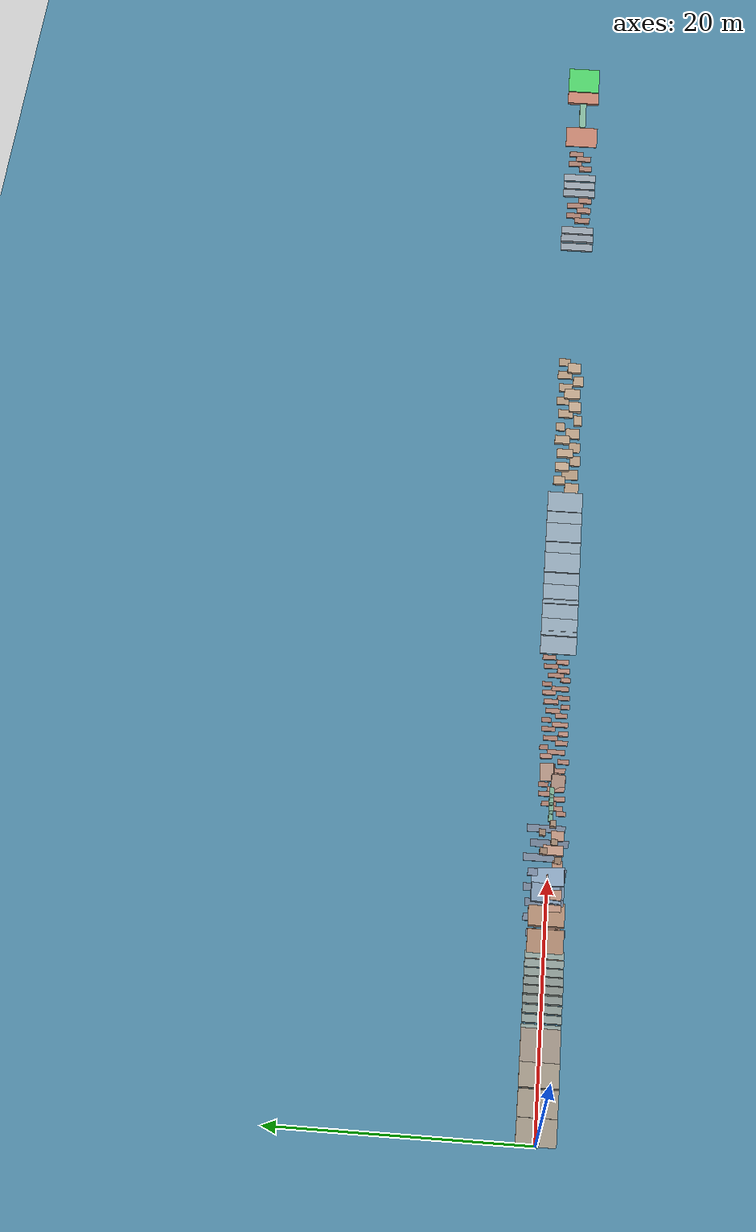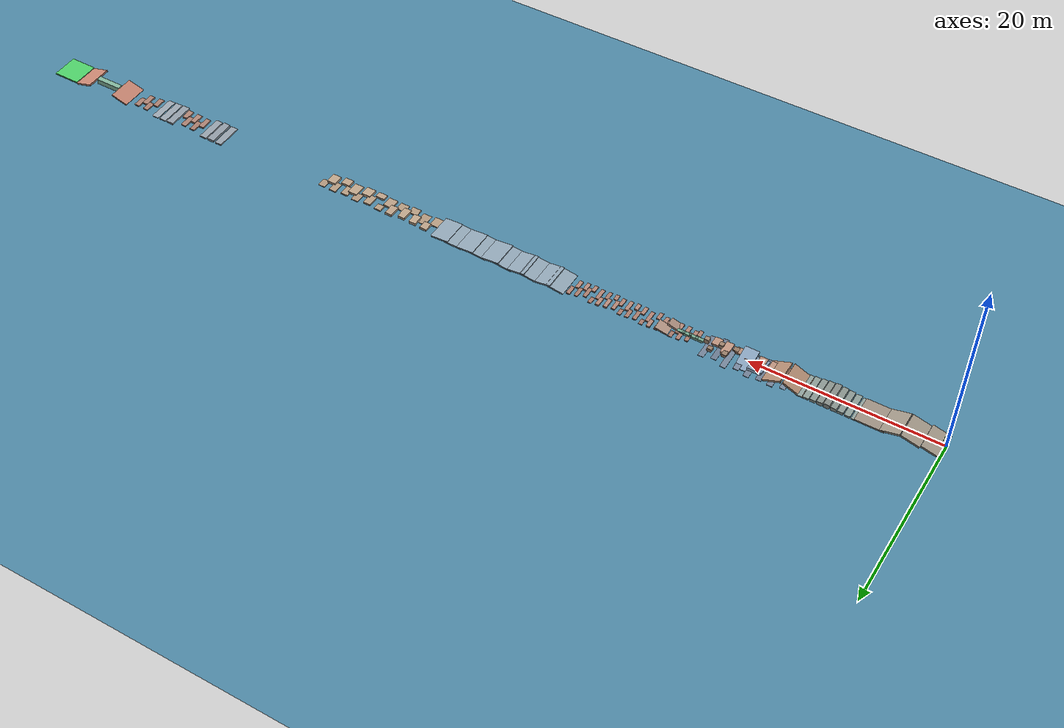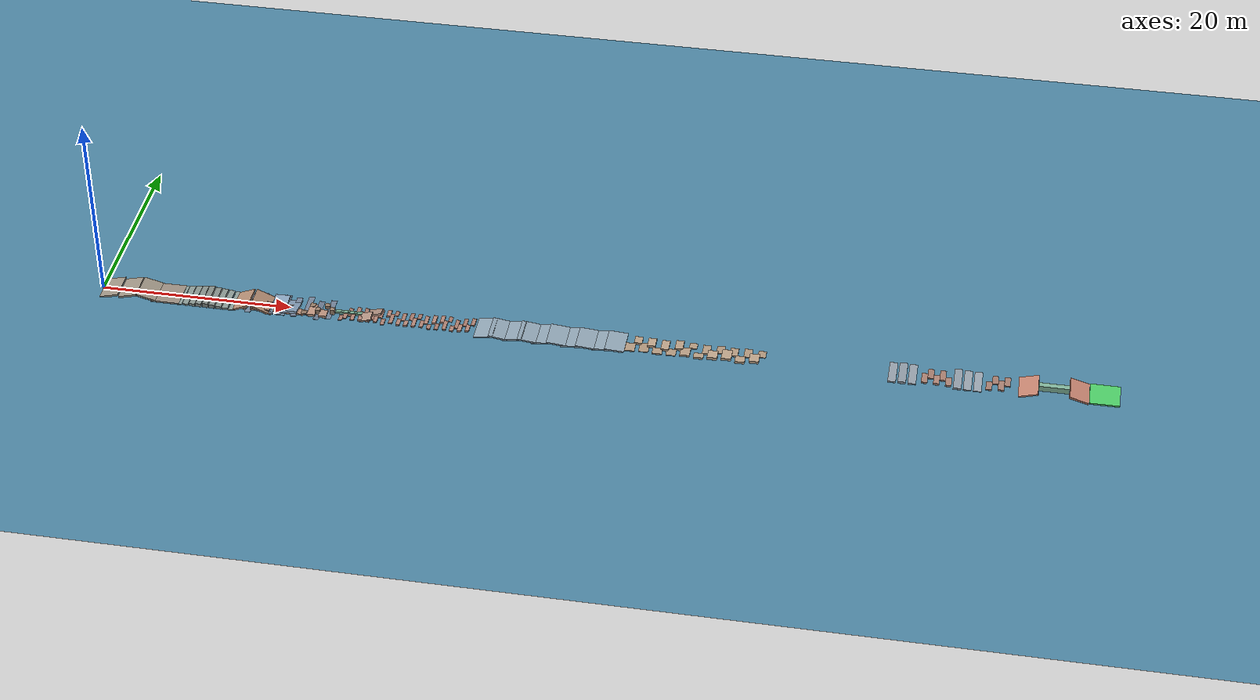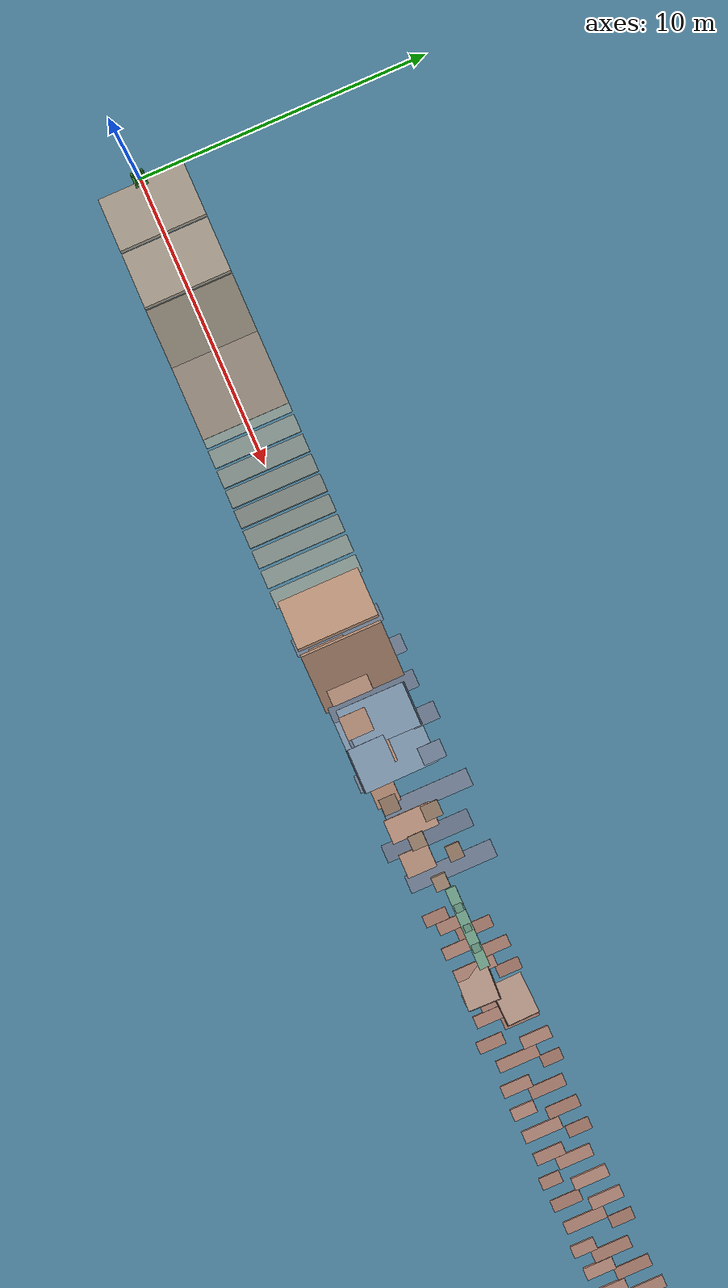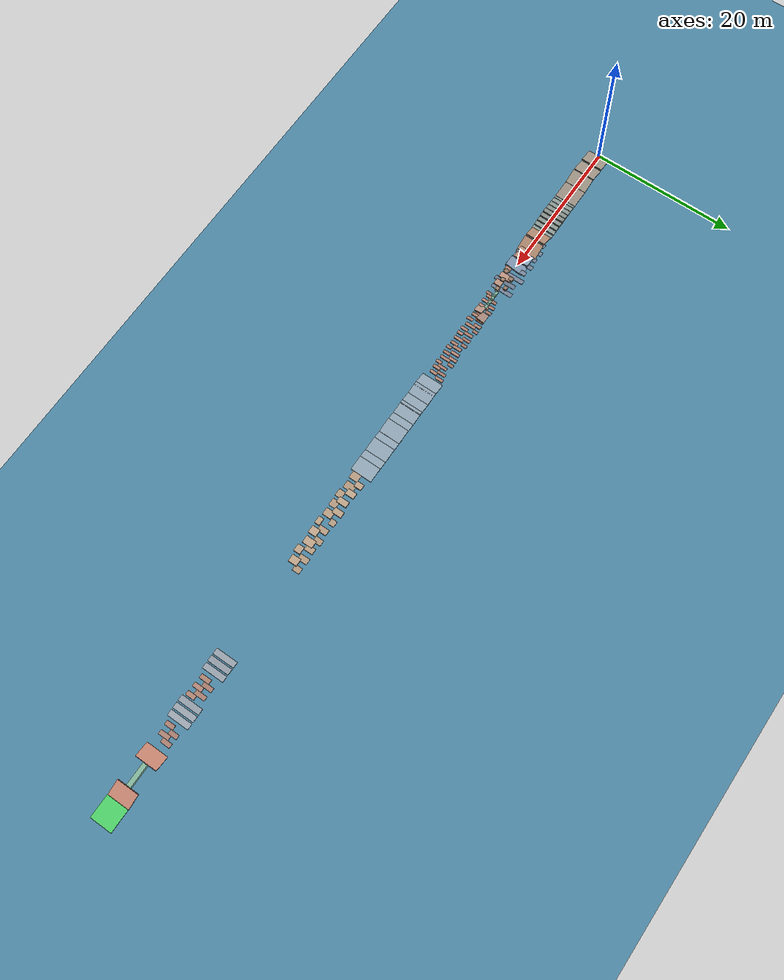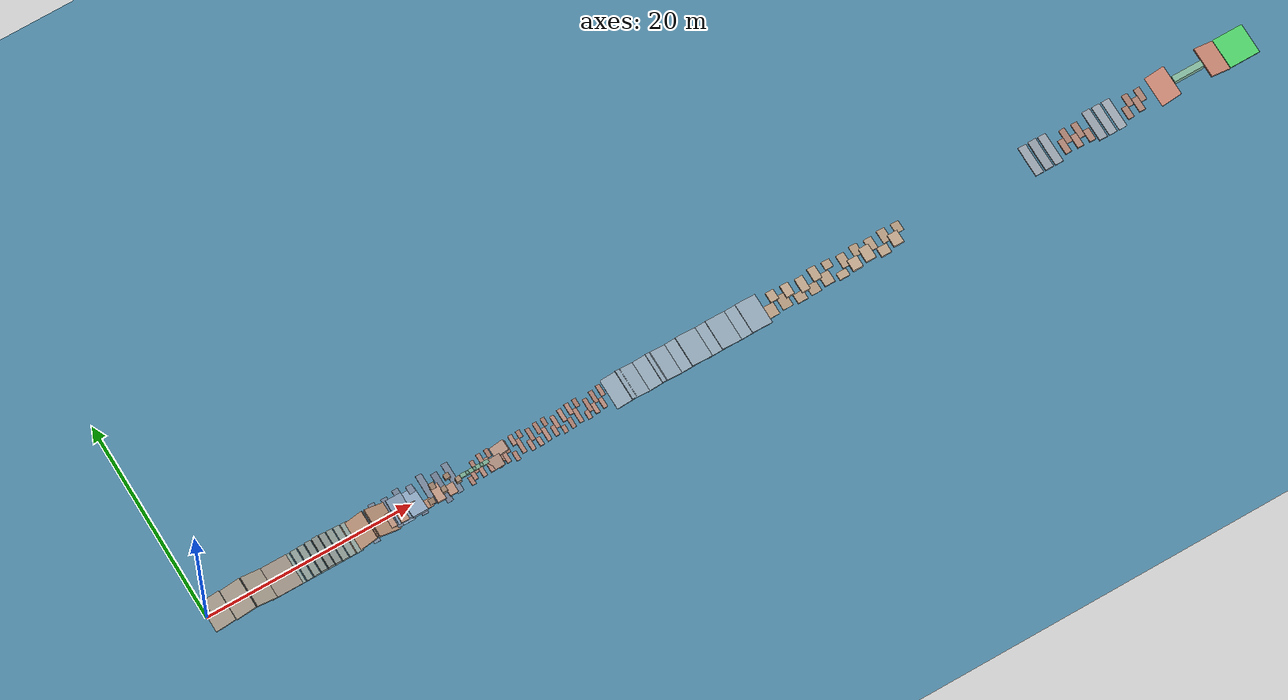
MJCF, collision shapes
<mujoco model="elf3">
  <compiler angle="radian" meshdir="../meshes" autolimits="true"/>

  <default>
    <default class="elf3">
      <joint frictionloss="0.1" solimplimit="0.97 0.995 0.001" armature="0.01"/>
      <default class="visual">
        <geom group="2" type="mesh" density="0" material="silver" contype="0" conaffinity="0"/>
      </default>
      <default class="collision">
        <geom group="3" rgba=".2 .6 .2 .3" type="capsule" contype="1" conaffinity="1"/>
        <default class="foot_capsule">
          <geom type="capsule" size="0.015"/>
        </default>
      </default>
      <site group="5" rgba="1 0 0 1"/>
    </default>
  </default>

  <asset>
    <material name="silver" rgba="0.7 0.7 0.7 1"/>
    <material name="black" rgba="0.2 0.2 0.2 1"/>

    <mesh name="torso_link" file="torso_link.STL"/>

    <mesh name="waist_y_link" file="waist_y_link.STL"/>
    <mesh name="waist_x_link" file="waist_x_link.STL"/>
    <mesh name="waist_z_link" file="waist_z_link.STL"/>

    <mesh name="l_hip_y_link" file="l_hip_y_link.STL"/>
    <mesh name="l_hip_x_link" file="l_hip_x_link.STL"/>
    <mesh name="l_hip_z_link" file="l_hip_z_link.STL"/>
    <mesh name="l_knee_y_link" file="l_knee_y_link.STL"/>
    <mesh name="l_ankle_y_link" file="l_ankle_y_link.STL"/>
    <mesh name="l_ankle_x_link" file="l_ankle_x_link.STL"/>

    <mesh name="r_hip_y_link" file="r_hip_y_link.STL"/>
    <mesh name="r_hip_x_link" file="r_hip_x_link.STL"/>
    <mesh name="r_hip_z_link" file="r_hip_z_link.STL"/>
    <mesh name="r_knee_y_link" file="r_knee_y_link.STL"/>
    <mesh name="r_ankle_y_link" file="r_ankle_y_link.STL"/>
    <mesh name="r_ankle_x_link" file="r_ankle_x_link.STL"/>

    <mesh name="l_shoulder_y_link" file="l_shoulder_y_link.STL"/>
    <mesh name="l_shoulder_x_link" file="l_shoulder_x_link.STL"/>
    <mesh name="l_shoulder_z_link" file="l_shoulder_z_link.STL"/>
    <mesh name="l_elbow_y_link" file="l_elbow_y_link.STL"/>
    <mesh name="l_wrist_x_link" file="l_wrist_x_link.STL"/>
    <mesh name="l_wrist_y_link" file="l_wrist_y_link.STL"/>
    <mesh name="l_wrist_z_link" file="l_hand.STL"/>

    <mesh name="r_shoulder_y_link" file="r_shoulder_y_link.STL"/>
    <mesh name="r_shoulder_x_link" file="r_shoulder_x_link.STL"/>
    <mesh name="r_shoulder_z_link" file="r_shoulder_z_link.STL"/>
    <mesh name="r_elbow_y_link" file="r_elbow_y_link.STL"/>
    <mesh name="r_wrist_x_link" file="r_wrist_x_link.STL"/>
    <mesh name="r_wrist_y_link" file="r_wrist_y_link.STL"/>
    <mesh name="r_wrist_z_link" file="r_hand.STL"/>

  </asset>

  <worldbody>
    <body name="torso_link" pos="0 0 1.1" childclass="elf3">
      <light pos="0 0 2" mode="trackcom"/>
      <camera name="tracking" pos="-2.5 0.0 1.1" euler="0 -1.04 -1.57" mode="trackcom"/>
      <camera name="head_camera" mode="fixed" pos="-0.4 0 0.8" euler="0 -1.04 -1.57" fovy="90"/>
      <inertial pos="0.001601 0.000219 0.023250" mass="12.004" fullinertia="0.2931669 0.26589586 0.06116338 -0.00014022 0.00019310 -0.00056456"/>
      <geom class="visual" type="mesh" rgba="0.75294 0.75294 0.75294 1" mesh="torso_link"/>
       <joint name="world_joint" type="free"/>
       <site name="imu_in_pelvis" size="0.01" pos="0.0 0 0.0"/>
      <!-- fromto="ux uy uz lx ly lz" -->
      <geom name="torso_collision" class="collision" size="0.09" fromto="0.0 0 -0.12 0.0 0 0.08"/>
      <geom name="torso_2_collision" class="collision" size="0.08" fromto="0.0 -0.025 -0.12   0.0 0.025 -0.12"/>
      <geom name="head_collision" class="collision" size="0.065" fromto="-0.01 0.00 0.30 0.02 0.00 0.30"/>

      <!-- Waist Chain -->
      <body name="waist_y_link" pos="0 0 -0.2265">
        <inertial pos="0 0 0" quat="0 0.707107 0 0.707107" mass="0.0661518" diaginertia="2.799e-05 1.845e-05 1.104e-05"/>
        <joint name="waist_y_joint" pos="0 0 0" axis="0 1 0" range="-0.5236 0.5236" damping="5.0"/>
        <geom class="visual" type="mesh" rgba="0.752941 0.752941 0.752941 1" mesh="waist_y_link"/>

        <body name="waist_x_link">
          <inertial pos="-0.0105041 6.39183e-08 -0.0167973" quat="0 0.79615 0 0.605099" mass="0.215643" diaginertia="0.000266195 0.00017942 0.000134265"/>
          <joint name="waist_x_joint" pos="0 0 0" axis="1 0 0" range="-0.2618 0.2618" damping="5.0"/>
          <geom class="visual" type="mesh" rgba="0.752941 0.752941 0.752941 1" mesh="waist_x_link"/>

          <body name="waist_z_link">
            <inertial pos="-1.01283e-06 1.1248e-05 -0.126152" quat="1 6.14768e-11 -6.32993e-05 -9.71208e-07" mass="4.95603" diaginertia="0.0210971 0.0159488 0.013672"/>
            <joint name="waist_z_joint" pos="0 0 0" axis="0 0 1" range="-2.8798 2.8798" damping="5.0"/>
            <geom class="visual" type="mesh" rgba="0.752941 0.752941 0.752941 1" mesh="waist_z_link" />

            <geom name="waist_z_1_collision" class="collision" size="0.055" fromto="0 -0.03 -0.156   0 0.03 -0.156"/>
            <geom name="waist_z_2_collision" class="collision" size="0.055" fromto="0 0 -0.156   0 0 -0.05"/>

            <!-- l Leg Chain -->
            <body name="l_hip_y_link" pos="0 0.136 -0.156">
              <inertial pos="-0.021777 -0.00277946 0.000699282" quat="0.796416 0.601232 0.0517671 0.039512" mass="1.70385" diaginertia="0.00281533 0.00218511 0.0019944"/>
              <joint name="l_hip_y_joint" pos="0 0 0" axis="0 1 0" range="-2.8798 2.8798" damping="3.0"/>
              <geom class="visual" type="mesh" rgba="0.752941 0.752941 0.752941 1" mesh="l_hip_y_link" />

              <body name="l_hip_x_link">
                <inertial pos="0.0163074 1.05982e-08 -0.0384681" quat="0.997755 0 0.066975 0" mass="0.214152" diaginertia="0.000346601 0.00030038 0.000125989"/>
                <joint name="l_hip_x_joint" pos="0 0 0" axis="1 0 0" range="-0.48869 3.0543" damping="3.0"/>
                <geom class="visual" type="mesh" rgba="0.752941 0.752941 0.752941 1" mesh="l_hip_x_link" pos="0 0 -0.03" />
                <geom name="l_hip_x_collision" class="collision" size="0.05" fromto="-0.035 0 0   0.0 0 0"/>
                <body name="l_hip_z_link">
                  <inertial pos="0.00128858 -0.00894579 -0.233969" quat="0.684622 -0.027855 0.0299671 0.727749" mass="2.84278" diaginertia="0.0321197 0.031121 0.0032734"/>
                  <joint name="l_hip_z_joint" pos="0 0 0" axis="0 0 1" range="-2.8798 2.8798" damping="2.0"/>
                  <geom class="visual" type="mesh" rgba="0.752941 0.752941 0.752941 1" mesh="l_hip_z_link" pos="0 0 -0.03" />
                  <geom name="l_hip_z_1_collision" class="collision" size="0.05" fromto="0.0 0 -0.12   0.0 0 -0.35"/>
                  <geom name="l_hip_z_2_collision" class="collision" size="0.05" fromto="0.0 -0.025 -0.35   0.0 0 -0.35"/>
                  <body name="l_knee_y_link" pos="0 0 -0.35">
                    <inertial pos="0.00743378 0.00339915 -0.143783" quat="0.824886 -0.0250601 0.0341455 0.563709" mass="1.77391" diaginertia="0.00878814 0.00856731 0.00138834"/>
                    <joint name="l_knee_y_joint" pos="0 0 0" axis="0 1 0" range="-0.087266 2.618" damping="2.0"/>
                    <geom class="visual" type="mesh" rgba="0.752941 0.752941 0.752941 1" mesh="l_knee_y_link" pos="0 0 -0.03" />
                    <geom name="l_knee_y_collision" class="collision" size="0.05" fromto="0.0 0 -0.15   0.0 0 -0.29"/>

                    <body name="l_ankle_y_link" pos="0 0 -0.32">
                      <inertial pos="0 0 -4.1832e-09" quat="0.5 0.5 -0.5 0.5" mass="0.0126899" diaginertia="1.55e-06 1.31e-06 5.9e-07"/>
                      <joint name="l_ankle_y_joint" pos="0 0 0" axis="0 1 0" range="-0.87266 0.7854" damping="1.0"/>
                      <geom class="visual" type="mesh" rgba="0.752941 0.752941 0.752941 1" mesh="l_ankle_y_link" pos="0 0 -0.03" />

                      <body name="l_ankle_x_link">
                        <inertial pos="0.0275442 6.46069e-10 -0.0292972" quat="0 0.713286 0 0.700873" mass="0.298065" diaginertia="0.00150765 0.00138193 0.000163046"/>
                        <joint name="l_ankle_x_joint" pos="0 0 0" axis="1 0 0" range="-0.34907 0.34907" damping="1.0"/>
                        <geom class="visual" type="mesh" rgba="0.752941 0.752941 0.752941 1" mesh="l_ankle_x_link" pos="0 0 -0.03" />
                        <site name="lf_tc" pos="0.05 0 -0.08" size="0.01" />
                        <geom name="l_foot1_collision" class="foot_capsule" fromto="0.12 -0.026 -0.055 -0.05 -0.027 -0.055"/>
                        <geom name="l_foot2_collision" class="foot_capsule" fromto="-0.068 -0.018 -0.055 0.127 -0.018 -0.055"/>
                        <geom name="l_foot3_collision" class="foot_capsule" fromto="-0.072 -0.01 -0.055 0.13 -0.01 -0.055"/>
                        <geom name="l_foot4_collision" class="foot_capsule" fromto="-0.074 0 -0.055 0.132 0 -0.055"/>
                        <geom name="l_foot5_collision" class="foot_capsule" fromto="-0.072 0.01 -0.055 0.13 0.01 -0.055"/>
                        <geom name="l_foot6_collision" class="foot_capsule" fromto="-0.068 0.018 -0.055 0.127 0.018 -0.055"/>
                        <geom name="l_foot7_collision" class="foot_capsule" fromto="0.12 0.026 -0.055 -0.05 0.026 -0.055"/>
                      </body>
                    </body>
                  </body>
                </body>
              </body>
            </body>

            <!-- r Leg Chain -->
            <body name="r_hip_y_link" pos="0 -0.136 -0.156">
              <inertial pos="-0.021777 0.00272279 0.000732" quat="0.602526 0.795307 -0.042061 -0.0517694" mass="1.70385" diaginertia="0.00281648 0.0021855 0.00199374"/>
              <joint name="r_hip_y_joint" pos="0 0 0" axis="0 1 0" range="-2.8798 2.8798" damping="3.0"/>
              <geom class="visual" type="mesh" rgba="0.752941 0.752941 0.752941 1" mesh="r_hip_y_link" />

              <body name="r_hip_x_link">
                <inertial pos="0.0163074 1.05982e-08 -0.0384681" quat="0.997755 0 0.066975 0" mass="0.214152" diaginertia="0.000346601 0.00030038 0.000125989"/>
                <joint name="r_hip_x_joint" pos="0 0 0" axis="1 0 0" range="-3.0543 0.48869" damping="3.0"/>
                <geom class="visual" type="mesh" rgba="0.752941 0.752941 0.752941 1" mesh="r_hip_x_link" pos="0 0 -0.03" />
                <geom name="r_hip_x_collision" class="collision" size="0.05" fromto="-0.035 0 0   0.0 0 0"/>

                <body name="r_hip_z_link">
                  <inertial pos="0.00128913 0.00895213 -0.233968" quat="0.727741 0.0299428 -0.0278367 0.684632" mass="2.84278" diaginertia="0.0321189 0.0311203 0.00327334"/>
                  <joint name="r_hip_z_joint" pos="0 0 0" axis="0 0 1" range="-2.8798 2.8798" damping="2.0"/>
                  <geom class="visual" type="mesh" rgba="0.752941 0.752941 0.752941 1" mesh="r_hip_z_link" pos="0 0 -0.03" />
                  <geom name="r_hip_z_1_collision" class="collision" size="0.05" fromto="0.0 0 -0.12   0.0 0 -0.35"/>
                  <geom name="r_hip_z_2_collision" class="collision" size="0.05" fromto="0.0 0.025 -0.35   0.0 0 -0.35"/>
                  <body name="r_knee_y_link" pos="0 0 -0.35">
                    <inertial pos="0.00743378 -0.00337367 -0.143783" quat="0.561231 0.034056 -0.025158 0.826576" mass="1.77391" diaginertia="0.00878933 0.00856646 0.00138868"/>
                    <joint name="r_knee_y_joint" pos="0 0 0" axis="0 1 0" range="-0.087266 2.618" damping="2.0"/>
                    <geom class="visual" type="mesh" rgba="0.752941 0.752941 0.752941 1" mesh="r_knee_y_link" pos="0 0 -0.03" />
                    <geom name="r_knee_y_collision" class="collision" size="0.05" fromto="0.0 0 -0.15   0.0 0 -0.29"/>

                    <body name="r_ankle_y_link" pos="0 0 -0.32">
                      <inertial pos="0 0 -4.18322e-09" quat="0.5 0.5 -0.5 0.5" mass="0.0126899" diaginertia="1.55e-06 1.31e-06 5.9e-07"/>
                      <joint name="r_ankle_y_joint" pos="0 0 0" axis="0 1 0" range="-0.87266 0.7854" damping="1.0"/>
                      <geom class="visual" type="mesh" rgba="0.752941 0.752941 0.752941 1" mesh="r_ankle_y_link" pos="0 0 -0.03" />

                      <body name="r_ankle_x_link">
                        <inertial pos="0.0275442 6.46053e-10 -0.0292972" quat="0 0.713286 0 0.700873" mass="0.298065" diaginertia="0.00150765 0.00138193 0.000163046"/>
                        <joint name="r_ankle_x_joint" pos="0 0 0" axis="1 0 0" range="-0.34907 0.34907" damping="1.0"/>
                        <geom class="visual" type="mesh" rgba="0.752941 0.752941 0.752941 1" mesh="r_ankle_x_link" pos="0 0 -0.03" />
                        <site name="rf_tc" pos="0.05 0 -0.08" size="0.01" />
                        <geom name="r_foot1_collision" class="foot_capsule" fromto="0.12 -0.026 -0.055 -0.05 -0.027 -0.055"/>
                        <geom name="r_foot2_collision" class="foot_capsule" fromto="-0.068 -0.018 -0.055 0.127 -0.018 -0.055"/>
                        <geom name="r_foot3_collision" class="foot_capsule" fromto="-0.072 -0.01 -0.055 0.13 -0.01 -0.055"/>
                        <geom name="r_foot4_collision" class="foot_capsule" fromto="-0.074 0 -0.055 0.132 0 -0.055"/>
                        <geom name="r_foot5_collision" class="foot_capsule" fromto="-0.072 0.01 -0.055 0.13 0.01 -0.055"/>
                        <geom name="r_foot6_collision" class="foot_capsule" fromto="-0.068 0.018 -0.055 0.127 0.018 -0.055"/>
                        <geom name="r_foot7_collision" class="foot_capsule" fromto="0.12 0.026 -0.055 -0.05 0.026 -0.055"/>
                      </body>
                    </body>
                  </body>
                </body>
              </body>
            </body>
          </body>
        </body>
      </body>

      <!-- l Arm Chain -->
      <body name="l_shoulder_y_link" pos="0 0.178 0.087">
        <inertial pos="-0.0194828 -0.00304252 0.000461368" quat="0.751186 0.652944 0.0750571 0.0612398" mass="0.938483" diaginertia="0.00102195 0.000817739 0.000721669"/>
        <joint name="l_shoulder_y_joint" pos="0 0 0" axis="0 1 0" range="-2.8798 2.8798" damping="2.0"/>
        <geom class="visual" type="mesh" rgba="0.752941 0.752941 0.752941 1" mesh="l_shoulder_y_link" />

        <body name="l_shoulder_x_link">
          <inertial pos="0.00939873 1.86326e-09 -0.0272171" quat="0.994844 0 0.101416 0" mass="0.130651" diaginertia="0.000139965 0.00011597 5.88054e-05"/>
          <joint name="l_shoulder_x_joint" pos="0 0 0" axis="1 0 0" range="-0.34907 3.0543" damping="2.0"/>
          <geom class="visual" type="mesh" rgba="0.752941 0.752941 0.752941 1" mesh="l_shoulder_x_link" />
          <geom name="l_shoulder_x_collision" class="collision" size="0.04" fromto="-0.03 0 0   0.0 0 0"/>
          <body name="l_shoulder_z_link">
            <inertial pos="-0.000948901 -0.00269014 -0.207899" quat="0.734549 -0.0171253 0.014469 0.678185" mass="1.29694" diaginertia="0.00804984 0.00776246 0.000985623"/>
            <joint name="l_shoulder_z_joint" pos="0 0 0" axis="0 0 1" range="-2.8798 2.8798" damping="1.5"/>
            <geom class="visual" type="mesh" rgba="0.752941 0.752941 0.752941 1" mesh="l_shoulder_z_link" />
            <geom name="l_shoulder_z_1_collision" class="collision" size="0.035" fromto="0 0 -0.08   0 0 -0.27"/>
            <geom name="l_shoulder_z_2_collision" class="collision" size="0.04" fromto="0 -0.015 -0.256   0 0.01 -0.256"/>

            <body name="l_elbow_y_link" pos="0 0 -0.256">
              <inertial pos="0.0294656 0.0164098 -3.34e-10" quat="0.5 0.5 0.5 0.5" mass="0.0938669" diaginertia="8.534e-05 8.443e-05 4.361e-05"/>
              <joint name="l_elbow_y_joint" pos="0 0 0" axis="0 1 0" range="-0.95993 1.6581" damping="1.0"/>
              <geom class="visual" type="mesh" rgba="0.752941 0.752941 0.752941 1" mesh="l_elbow_y_link" />
              <geom name="l_elbow_y_collision" class="collision" size="0.04" fromto="0.08 0 0   0.2 0 0"/>

              <body name="l_wrist_x_link" pos="0.256 0 0">
                <inertial pos="-0.124483 -0.00110033 3.42813e-05" quat="0.5 0.5 0.5 0.5" mass="0.658675" diaginertia="0.00208306 0.001834 0.00054605"/>
                <joint name="l_wrist_x_joint" pos="0 0 0" axis="1 0 0" range="-2.8798 2.8798" damping="0.5"/>
                <geom class="visual" type="mesh" rgba="0.752941 0.752941 0.752941 1" mesh="l_wrist_x_link"/>

                <body name="l_wrist_y_link">
                  <inertial pos="-1.24357e-05 -0.000129932 -0.00298556" quat="0.707107 0 0 0.707107" mass="0.243805" diaginertia="0.00018676 0.00018369 0.00014174"/>
                  <joint name="l_wrist_y_joint" pos="0 0 0" axis="0 1 0" range="-1.309 1.309" damping="0.5"/>
                  <geom class="visual" type="mesh" rgba="0.752941 0.752941 0.752941 1" mesh="l_wrist_y_link"/>

                  <body name="l_wrist_z_link">
                    <inertial pos="0.0308695 1.39176e-09 0.0141752" quat="0.92388 0 0.382683 0" mass="0.106561" diaginertia="8.685e-05 7.12e-05 7.068e-05"/>
                    <joint name="l_wrist_z_joint" pos="0 0 0" axis="0 0 1" range="-0.7854 0.7854" damping="0.5"/>
                    <geom class="visual" type="mesh" rgba="0.752941 0.752941 0.752941 1" mesh="l_wrist_z_link"/>
                    <geom name="l_wrist_z_collision" class="collision" type="sphere" size="0.03" pos="0.04 0 0"/>
                    <geom name="l_wrist_z_collision2" class="collision" type="sphere" size="0.05" pos="0.11 -0.01 0"/>
                  </body>
                </body>
              </body>
            </body>
          </body>
        </body>
      </body>

      <!-- r Arm Chain -->
      <body name="r_shoulder_y_link" pos="0 -0.178 0.087">
        <inertial pos="-0.0194828 0.00304195 0.00046038" quat="0.652921 0.751201 -0.0612164 -0.0751263" mass="0.938483" diaginertia="0.00102196 0.000817748 0.00072166"/>
        <joint name="r_shoulder_y_joint" pos="0 0 0" axis="0 1 0" range="-2.8798 2.8798" damping="2.0"/>
        <geom class="visual" type="mesh" rgba="0.752941 0.752941 0.752941 1" mesh="r_shoulder_y_link" />

        <body name="r_shoulder_x_link">
          <inertial pos="0.00939873 1.86336e-09 -0.0272171" quat="0.994844 0 0.101416 0" mass="0.130651" diaginertia="0.000139965 0.00011597 5.88054e-05"/>
          <joint name="r_shoulder_x_joint" pos="0 0 0" axis="1 0 0" range="-3.0543 0.34907" damping="2.0"/>
          <geom class="visual" type="mesh" rgba="0.752941 0.752941 0.752941 1" mesh="r_shoulder_x_link" />
          <geom name="r_shoulder_x_collision" class="collision" size="0.04" fromto="-0.03 0 0   0.0 0 0"/>
          <body name="r_shoulder_z_link">
            <inertial pos="-0.000936876 0.00267273 -0.207892" quat="0.677531 0.014495 -0.0172678 0.735148" mass="1.29694" diaginertia="0.00804923 0.00776163 0.000985616"/>
            <joint name="r_shoulder_z_joint" pos="0 0 0" axis="0 0 1" range="-2.8798 2.8798" damping="1.5"/>
            <geom class="visual" type="mesh" rgba="0.752941 0.752941 0.752941 1" mesh="r_shoulder_z_link" />
            <geom name="r_shoulder_z_1_collision" class="collision" size="0.035" fromto="0 0 -0.08   0 0 -0.27"/>
            <geom name="r_shoulder_z_2_collision" class="collision" size="0.04" fromto="0 0.015 -0.256   0 -0.01 -0.256"/>

            <body name="r_elbow_y_link" pos="0 0 -0.256">
              <inertial pos="0.0294656 -0.0164098 -6.94346e-10" quat="0.5 0.5 0.5 0.5" mass="0.0938669" diaginertia="8.534e-05 8.443e-05 4.361e-05"/>
              <joint name="r_elbow_y_joint" pos="0 0 0" axis="0 1 0" range="-0.95993 1.6581" damping="1.0"/>
              <geom class="visual" type="mesh" rgba="0.752941 0.752941 0.752941 1" mesh="r_elbow_y_link" />
              <geom name="r_elbow_y_collision" class="collision" size="0.04" fromto="0.08 0 0   0.2 0 0"/>

              <body name="r_wrist_x_link" pos="0.256 0 0">
                <inertial pos="-0.124486 0.00109279 3.42822e-05" quat="0.5 0.5 0.5 0.5" mass="0.658675" diaginertia="0.0020829 0.00183383 0.00054606"/>
                <joint name="r_wrist_x_joint" pos="0 0 0" axis="1 0 0" range="-2.8798 2.8798" damping="0.5"/>
                <geom class="visual" type="mesh" rgba="0.752941 0.752941 0.752941 1" mesh="r_wrist_x_link"/>

                <body name="r_wrist_y_link">
                  <inertial pos="-7.9397e-06 3.73154e-05 -0.00298556" quat="0.707107 0 0 0.707107" mass="0.243805" diaginertia="0.00018676 0.00018369 0.00014174"/>
                  <joint name="r_wrist_y_joint" pos="0 0 0" axis="0 1 0" range="-1.309 1.309" damping="0.5"/>
                  <geom class="visual" type="mesh" rgba="0.752941 0.752941 0.752941 1" mesh="r_wrist_y_link"/>

                  <body name="r_wrist_z_link">
                    <inertial pos="0.0308695 1.11972e-09 0.0141752" quat="0.92388 0 0.382683 0" mass="0.106561" diaginertia="8.685e-05 7.12e-05 7.068e-05"/>
                    <joint name="r_wrist_z_joint" pos="0 0 0" axis="0 0 1" range="-0.7854 0.7854" damping="0.5"/>
                    <geom class="visual" type="mesh" rgba="0.752941 0.752941 0.752941 1" mesh="r_wrist_z_link"/>
                    <geom name="r_wrist_z_collision" class="collision" type="sphere" size="0.03" pos="0.04 0 0"/>
                    <geom name="r_wrist_z_collision2" class="collision" type="sphere" size="0.05" pos="0.11 0.01 0"/>
                  </body>
                </body>
              </body>
            </body>
          </body>
        </body>
      </body>
    </body>
  </worldbody>

  <contact>

    <!-- l foot - floor -->
    <pair name="l_foot1_floor" geom1="l_foot1_collision" geom2="floor" solref="0.01 1" friction="0.8 0.8"/>
    <pair name="l_foot2_floor" geom1="l_foot2_collision" geom2="floor" solref="0.01 1" friction="0.8 0.8"/>
    <pair name="l_foot3_floor" geom1="l_foot3_collision" geom2="floor" solref="0.01 1" friction="0.8 0.8"/>
    <pair name="l_foot4_floor" geom1="l_foot4_collision" geom2="floor" solref="0.01 1" friction="0.8 0.8"/>
    <pair name="l_foot5_floor" geom1="l_foot5_collision" geom2="floor" solref="0.01 1" friction="0.8 0.8"/>
    <pair name="l_foot6_floor" geom1="l_foot6_collision" geom2="floor" solref="0.01 1" friction="0.8 0.8"/>
    <pair name="l_foot7_floor" geom1="l_foot7_collision" geom2="floor" solref="0.01 1" friction="0.8 0.8"/>
    <!-- r foot - floor -->
    <pair name="r_foot1_floor" geom1="r_foot1_collision" geom2="floor" solref="0.01 1" friction="0.8 0.8"/>
    <pair name="r_foot2_floor" geom1="r_foot2_collision" geom2="floor" solref="0.01 1" friction="0.8 0.8"/>
    <pair name="r_foot3_floor" geom1="r_foot3_collision" geom2="floor" solref="0.01 1" friction="0.8 0.8"/>
    <pair name="r_foot4_floor" geom1="r_foot4_collision" geom2="floor" solref="0.01 1" friction="0.8 0.8"/>
    <pair name="r_foot5_floor" geom1="r_foot5_collision" geom2="floor" solref="0.01 1" friction="0.8 0.8"/>
    <pair name="r_foot6_floor" geom1="r_foot6_collision" geom2="floor" solref="0.01 1" friction="0.8 0.8"/>
    <pair name="r_foot7_floor" geom1="r_foot7_collision" geom2="floor" solref="0.01 1" friction="0.8 0.8"/>

  </contact>

  <actuator>
    <motor name="waist_y_joint" joint="waist_y_joint" gear="1" ctrllimited='true' ctrlrange='-100 100'/>
    <motor name="waist_x_joint" joint="waist_x_joint" gear="1" ctrllimited='true' ctrlrange='-100 100'/>
    <motor name="waist_z_joint" joint="waist_z_joint" gear="1" ctrllimited='true' ctrlrange='-100 100'/>

    <motor name="l_hip_y_joint" joint="l_hip_y_joint" gear="1" ctrllimited='true' ctrlrange='-100 100'/>
    <motor name="l_hip_x_joint" joint="l_hip_x_joint" gear="1" ctrllimited='true' ctrlrange='-100 100'/>
    <motor name="l_hip_z_joint" joint="l_hip_z_joint" gear="1" ctrllimited='true' ctrlrange='-50 50'/>
    <motor name="l_knee_y_joint" joint="l_knee_y_joint" gear="1" ctrllimited='true' ctrlrange='-150 150'/>
    <motor name="l_ankle_y_joint" joint="l_ankle_y_joint" gear="1" ctrllimited='true' ctrlrange='-50 50'/>
    <motor name="l_ankle_x_joint" joint="l_ankle_x_joint" gear="1" ctrllimited='true' ctrlrange='-20 20'/>

    <motor name="r_hip_y_joint" joint="r_hip_y_joint" gear="1" ctrllimited='true' ctrlrange='-100 100'/>
    <motor name="r_hip_x_joint" joint="r_hip_x_joint" gear="1" ctrllimited='true' ctrlrange='-100 100'/>
    <motor name="r_hip_z_joint" joint="r_hip_z_joint" gear="1" ctrllimited='true' ctrlrange='-50 50'/>
    <motor name="r_knee_y_joint" joint="r_knee_y_joint" gear="1" ctrllimited='true' ctrlrange='-150 150'/>
    <motor name="r_ankle_y_joint" joint="r_ankle_y_joint" gear="1" ctrllimited='true' ctrlrange='-50 50'/>
    <motor name="r_ankle_x_joint" joint="r_ankle_x_joint" gear="1" ctrllimited='true' ctrlrange='-20 20'/>

    <motor name="l_shoulder_y_joint" joint="l_shoulder_y_joint" gear="1" ctrllimited='true' ctrlrange='-50 50'/>
    <motor name="l_shoulder_x_joint" joint="l_shoulder_x_joint" gear="1" ctrllimited='true' ctrlrange='-50 50'/>
    <motor name="l_shoulder_z_joint" joint="l_shoulder_z_joint" gear="1" ctrllimited='true' ctrlrange='-25 25'/>
    <motor name="l_elbow_y_joint" joint="l_elbow_y_joint" gear="1" ctrllimited='true' ctrlrange='-50 50'/>
    <motor name="l_wrist_x_joint" joint="l_wrist_x_joint" gear="1" ctrllimited='true' ctrlrange='-25 25'/>
    <motor name="l_wrist_y_joint" joint="l_wrist_y_joint" gear="1" ctrllimited='true' ctrlrange='-25 25'/>
    <motor name="l_wrist_z_joint" joint="l_wrist_z_joint" gear="1" ctrllimited='true' ctrlrange='-25 25'/>

    <motor name="r_shoulder_y_joint" joint="r_shoulder_y_joint" gear="1" ctrllimited='true' ctrlrange='-50 50'/>
    <motor name="r_shoulder_x_joint" joint="r_shoulder_x_joint" gear="1" ctrllimited='true' ctrlrange='-50 50'/>
    <motor name="r_shoulder_z_joint" joint="r_shoulder_z_joint" gear="1" ctrllimited='true' ctrlrange='-25 25'/>
    <motor name="r_elbow_y_joint" joint="r_elbow_y_joint" gear="1" ctrllimited='true' ctrlrange='-50 50'/>
    <motor name="r_wrist_x_joint" joint="r_wrist_x_joint" gear="1" ctrllimited='true' ctrlrange='-25 25'/>
    <motor name="r_wrist_y_joint" joint="r_wrist_y_joint" gear="1" ctrllimited='true' ctrlrange='-25 25'/>
    <motor name="r_wrist_z_joint" joint="r_wrist_z_joint" gear="1" ctrllimited='true' ctrlrange='-25 25'/>
  </actuator>

  <sensor>
    <gyro name="Body_Gyro" site="imu_in_pelvis"/>
    <framequat name="Body_Quat" objtype="site" objname="imu_in_pelvis"/>
    <velocimeter name="imu_lin_vel" site="imu_in_pelvis"/>
    <accelerometer name="Body_Acc" site="imu_in_pelvis"/>
    <subtreeangmom name="root_angmom" body="torso_link"/>

    <jointpos name="waist_y_joint_pos" joint="waist_y_joint" />
    <jointpos name="waist_x_joint_pos" joint="waist_x_joint" />
    <jointpos name="waist_z_joint_pos" joint="waist_z_joint" />

    <jointpos name="l_hip_y_joint_pos" joint="l_hip_y_joint" />
    <jointpos name="l_hip_x_joint_pos" joint="l_hip_x_joint" />
    <jointpos name="l_hip_z_joint_pos" joint="l_hip_z_joint" />
    <jointpos name="l_knee_y_joint_pos" joint="l_knee_y_joint" />
    <jointpos name="l_ankle_y_joint_pos" joint="l_ankle_y_joint" />
    <jointpos name="l_ankle_x_joint_pos" joint="l_ankle_x_joint" />

    <jointpos name="r_hip_y_joint_pos" joint="r_hip_y_joint" />
    <jointpos name="r_hip_x_joint_pos" joint="r_hip_x_joint" />
    <jointpos name="r_hip_z_joint_pos" joint="r_hip_z_joint" />
    <jointpos name="r_knee_y_joint_pos" joint="r_knee_y_joint" />
    <jointpos name="r_ankle_y_joint_pos" joint="r_ankle_y_joint" />
    <jointpos name="r_ankle_x_joint_pos" joint="r_ankle_x_joint" />

    <jointpos name="l_shoulder_y_joint_pos" joint="l_shoulder_y_joint" />
    <jointpos name="l_shoulder_x_joint_pos" joint="l_shoulder_x_joint" />
    <jointpos name="l_shoulder_z_joint_pos" joint="l_shoulder_z_joint" />
    <jointpos name="l_elbow_y_joint_pos" joint="l_elbow_y_joint" />
    <jointpos name="l_wrist_x_joint_pos" joint="l_wrist_x_joint" />
    <jointpos name="l_wrist_y_joint_pos" joint="l_wrist_y_joint" />
    <jointpos name="l_wrist_z_joint_pos" joint="l_wrist_z_joint" />

    <jointpos name="r_shoulder_y_joint_pos" joint="r_shoulder_y_joint" />
    <jointpos name="r_shoulder_x_joint_pos" joint="r_shoulder_x_joint" />
    <jointpos name="r_shoulder_z_joint_pos" joint="r_shoulder_z_joint" />
    <jointpos name="r_elbow_y_joint_pos" joint="r_elbow_y_joint" />
    <jointpos name="r_wrist_x_joint_pos" joint="r_wrist_x_joint" />
    <jointpos name="r_wrist_y_joint_pos" joint="r_wrist_y_joint" />
    <jointpos name="r_wrist_z_joint_pos" joint="r_wrist_z_joint" />

    <jointvel name="waist_y_joint_vel" joint="waist_y_joint" />
    <jointvel name="waist_x_joint_vel" joint="waist_x_joint" />
    <jointvel name="waist_z_joint_vel" joint="waist_z_joint" />

    <jointvel name="l_hip_y_joint_vel" joint="l_hip_z_joint" />
    <jointvel name="l_hip_x_joint_vel" joint="l_hip_x_joint" />
    <jointvel name="l_hip_z_joint_vel" joint="l_hip_y_joint" />
    <jointvel name="l_knee_y_joint_vel" joint="l_knee_y_joint" />
    <jointvel name="l_ankle_y_joint_vel" joint="l_ankle_y_joint" />
    <jointvel name="l_ankle_x_joint_vel" joint="l_ankle_x_joint" />

    <jointvel name="r_hip_y_joint_vel" joint="r_hip_z_joint" />
    <jointvel name="r_hip_x_joint_vel" joint="r_hip_x_joint" />
    <jointvel name="r_hip_z_joint_vel" joint="r_hip_y_joint" />
    <jointvel name="r_knee_y_joint_vel" joint="r_knee_y_joint" />
    <jointvel name="r_ankle_y_joint_vel" joint="r_ankle_y_joint" />
    <jointvel name="r_ankle_x_joint_vel" joint="r_ankle_x_joint" />

    <jointvel name="l_shoulder_y_joint_vel" joint="l_shoulder_y_joint" />
    <jointvel name="l_shoulder_x_joint_vel" joint="l_shoulder_x_joint" />
    <jointvel name="l_shoulder_z_joint_vel" joint="l_shoulder_z_joint" />
    <jointvel name="l_elbow_y_joint_vel" joint="l_elbow_y_joint" />
    <jointvel name="l_wrist_x_joint_vel" joint="l_wrist_x_joint" />
    <jointvel name="l_wrist_y_joint_vel" joint="l_wrist_y_joint" />
    <jointvel name="l_wrist_z_joint_vel" joint="l_wrist_z_joint" />

    <jointvel name="r_shoulder_y_joint_vel" joint="r_shoulder_y_joint" />
    <jointvel name="r_shoulder_x_joint_vel" joint="r_shoulder_x_joint" />
    <jointvel name="r_shoulder_z_joint_vel" joint="r_shoulder_z_joint" />
    <jointvel name="r_elbow_y_joint_vel" joint="r_elbow_y_joint" />
    <jointvel name="r_wrist_x_joint_vel" joint="r_wrist_x_joint" />
    <jointvel name="r_wrist_y_joint_vel" joint="r_wrist_y_joint" />
    <jointvel name="r_wrist_z_joint_vel" joint="r_wrist_z_joint" />

    <touch name="lf_touch" site="lf_tc" />
    <touch name="rf_touch" site="rf_tc" />

  </sensor>

  <include file="scene_bx.xml"/>
</mujoco>

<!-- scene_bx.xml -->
<mujoco model="bx scene">

  <statistic center="0 0 0.6" extent="1.3"/>

  <visual>
    <headlight diffuse="0.5 0.5 0.5" ambient="0.2 0.2 0.2" specular="0.9 0.9 0.9"/>
    <rgba haze="0.15 0.25 0.35 1"/>
    <global azimuth="200" elevation="-20"/>
  </visual>

  <asset>
    <texture type="skybox" builtin="flat" rgb1="0.3 0.5 0.7" rgb2="0 0 0" width="512" height="3072"/>
    <texture type="2d" name="groundplane" builtin="checker" mark="edge" rgb1="0.3 0.52 0.63" rgb2="0.3 0.52 0.63" markrgb="1 1 1" width="300" height="300"/>
    <material name="groundplane" texture="groundplane" texuniform="true" texrepeat="5 5" reflectance="0.2"/>

    <texture name="texplane" type="2d" builtin="checker" rgb1=".2 .3 .4" rgb2=".1 0.15 0.2"
        width="512" height="512" mark="cross" markrgb=".8 .8 .8"/>
    <texture name="texplane2" type="2d" builtin="checker" rgb1="1 0.3137 0.1843" rgb2="0.0 0.30196 0.38039"
        width="512" height="512" mark="cross" markrgb=".8 .8 .8"/>
    <material name="matplane" reflectance="0." texture="texplane" texrepeat="1 1" texuniform="true"/>
    <material name="matplane2" reflectance="0.1" texture="texplane2" texrepeat="1 1" texuniform="true"/>
    <hfield name='hf0' nrow='200' ncol='200' size="10 5 0.2 .1"/>
  </asset>

  <worldbody>
    <light pos="1 0 3.5" dir="0 0 -1" directional="true"/>
    <geom name="floor" size="0 0 0.05" type="plane" material="groundplane" group="0"/>

    <!-- =============================================== 100米直线闯关地形 =============================================== -->
    <!-- 总长度 105米，宽 3米，包含: 斜面/台阶/凹凸/崎岖/曲面/杂乱地面 -->

    <!-- 第1段(0-8m): 初始斜面区域 -->
    <geom name="sec1_ramp_up_1" pos="1.0 0 0.10" type="box" size="1.0 1.5 0.10" euler="0 -0.25 0" rgba="0.62 0.58 0.52 1" friction="1.0 0.05 0.01"/>
    <geom name="sec1_ramp_up_2" pos="3.0 0 0.35" type="box" size="1.0 1.5 0.10" euler="0 -0.25 0" rgba="0.62 0.58 0.52 1" friction="1.0 0.05 0.01"/>
    <geom name="sec1_ramp_down"  pos="5.0 0 0.35" type="box" size="1.0 1.5 0.10" euler="0 0.25 0"  rgba="0.62 0.58 0.52 1" friction="1.0 0.05 0.01"/>
    <geom name="sec1_flat"       pos="7.0 0 0.08" type="box" size="1.5 1.5 0.08" rgba="0.60 0.55 0.50 1"/>

    <!-- 第2段(8-16m): 台阶上升区 -->
    <geom name="sec2_step_1" pos="8.5 0 0.05" type="box" size="0.3 1.5 0.05" rgba="0.55 0.62 0.60 1"/>
    <geom name="sec2_step_2" pos="9.2 0 0.10" type="box" size="0.3 1.5 0.10" rgba="0.54 0.60 0.58 1"/>
    <geom name="sec2_step_3" pos="9.9 0 0.15" type="box" size="0.3 1.5 0.15" rgba="0.53 0.58 0.56 1"/>
    <geom name="sec2_step_4" pos="10.6 0 0.20" type="box" size="0.3 1.5 0.20" rgba="0.52 0.56 0.54 1"/>
    <geom name="sec2_step_5" pos="11.3 0 0.25" type="box" size="0.3 1.5 0.25" rgba="0.51 0.54 0.52 1"/>
    <geom name="sec2_step_6" pos="12.0 0 0.20" type="box" size="0.3 1.5 0.20" rgba="0.52 0.56 0.54 1"/>
    <geom name="sec2_step_7" pos="12.7 0 0.15" type="box" size="0.3 1.5 0.15" rgba="0.53 0.58 0.56 1"/>
    <geom name="sec2_step_8" pos="13.4 0 0.10" type="box" size="0.3 1.5 0.10" rgba="0.54 0.60 0.58 1"/>
    <geom name="sec2_step_9" pos="14.1 0 0.05" type="box" size="0.3 1.5 0.05" rgba="0.55 0.62 0.60 1"/>

    <!-- 第3段(16-25m): 凹凸不平地面 -->
    <geom name="sec3_bump_1" pos="15.2 -0.6 0.08" type="box" size="0.4 0.5 0.08" rgba="0.68 0.52 0.45 1"/>
    <geom name="sec3_dip_1"  pos="15.8  0.0 0.02" type="box" size="0.3 1.5 0.02" rgba="0.45 0.52 0.60 1"/>
    <geom name="sec3_bump_2" pos="16.4 -0.5 0.10" type="box" size="0.4 0.6 0.10" rgba="0.70 0.54 0.46 1"/>
    <geom name="sec3_dip_2"  pos="17.0  0.3 0.03" type="box" size="0.3 1.5 0.03" rgba="0.44 0.50 0.58 1"/>
    <geom name="sec3_bump_3" pos="17.6 -0.4 0.12" type="box" size="0.4 0.7 0.12" rgba="0.72 0.56 0.48 1"/>
    <geom name="sec3_dip_3"  pos="18.2  0.2 0.01" type="box" size="0.3 1.5 0.01" rgba="0.42 0.48 0.56 1"/>
    <geom name="sec3_bump_4" pos="18.8 -0.6 0.11" type="box" size="0.4 0.5 0.11" rgba="0.71 0.55 0.47 1"/>
    <geom name="sec3_dip_4"  pos="19.4  0.4 0.02" type="box" size="0.3 1.5 0.02" rgba="0.43 0.49 0.57 1"/>
    <geom name="sec3_bump_5" pos="20.0 -0.5 0.13" type="box" size="0.4 0.6 0.13" rgba="0.73 0.57 0.49 1"/>
    <geom name="sec3_dip_5"  pos="20.6  0.1 0.04" type="box" size="0.3 1.5 0.04" rgba="0.46 0.52 0.61 1"/>
    <geom name="sec3_bump_6" pos="21.2 -0.7 0.09" type="box" size="0.4 0.4 0.09" rgba="0.69 0.53 0.44 1"/>
    <geom name="sec3_dip_6"  pos="21.8  0.5 0.03" type="box" size="0.3 1.5 0.03" rgba="0.45 0.51 0.59 1"/>
    <geom name="sec3_bump_7" pos="22.4 -0.3 0.14" type="box" size="0.4 0.8 0.14" rgba="0.74 0.58 0.50 1"/>
    <geom name="sec3_dip_7"  pos="23.0  0.0 0.01" type="box" size="0.3 1.5 0.01" rgba="0.41 0.47 0.55 1"/>
    <geom name="sec3_bump_8" pos="23.6 -0.6 0.12" type="box" size="0.4 0.5 0.12" rgba="0.72 0.56 0.48 1"/>
    <geom name="sec3_dip_8"  pos="24.2  0.3 0.02" type="box" size="0.3 1.5 0.02" rgba="0.44 0.50 0.58 1"/>

    <!-- 第4段(25-40m): 崎岖路面(密集小凸块) -->
    <geom name="sec4_rough_1"  pos="25.5 -0.8 0.04" type="box" size="0.2 0.4 0.04" rgba="0.65 0.48 0.42 1"/>
    <geom name="sec4_rough_2"  pos="25.9 -0.4 0.07" type="box" size="0.2 0.5 0.07" rgba="0.67 0.50 0.44 1"/>
    <geom name="sec4_rough_3"  pos="26.3  0.2 0.05" type="box" size="0.2 0.6 0.05" rgba="0.64 0.47 0.41 1"/>
    <geom name="sec4_rough_4"  pos="26.7 -0.6 0.08" type="box" size="0.2 0.45 0.08" rgba="0.68 0.51 0.45 1"/>
    <geom name="sec4_rough_5"  pos="27.1  0.5 0.06" type="box" size="0.2 0.55 0.06" rgba="0.66 0.49 0.43 1"/>
    <geom name="sec4_rough_6"  pos="27.5 -0.3 0.09" type="box" size="0.2 0.7 0.09" rgba="0.69 0.52 0.46 1"/>
    <geom name="sec4_rough_7"  pos="27.9  0.7 0.04" type="box" size="0.2 0.4 0.04" rgba="0.63 0.46 0.40 1"/>
    <geom name="sec4_rough_8"  pos="28.3 -0.7 0.10" type="box" size="0.2 0.35 0.10" rgba="0.70 0.53 0.47 1"/>
    <geom name="sec4_rough_9"  pos="28.7  0.0 0.07" type="box" size="0.2 0.65 0.07" rgba="0.67 0.50 0.44 1"/>
    <geom name="sec4_rough_10" pos="29.1 -0.5 0.08" type="box" size="0.2 0.5 0.08" rgba="0.68 0.51 0.45 1"/>
    <geom name="sec4_rough_11" pos="29.5  0.4 0.05" type="box" size="0.2 0.6 0.05" rgba="0.64 0.47 0.41 1"/>
    <geom name="sec4_rough_12" pos="29.9 -0.8 0.06" type="box" size="0.2 0.45 0.06" rgba="0.66 0.49 0.43 1"/>
    <geom name="sec4_rough_13" pos="30.3  0.6 0.09" type="box" size="0.2 0.5 0.09" rgba="0.69 0.52 0.46 1"/>
    <geom name="sec4_rough_14" pos="30.7 -0.2 0.07" type="box" size="0.2 0.7 0.07" rgba="0.67 0.50 0.44 1"/>
    <geom name="sec4_rough_15" pos="31.1  0.8 0.04" type="box" size="0.2 0.35 0.04" rgba="0.63 0.46 0.40 1"/>
    <geom name="sec4_rough_16" pos="31.5 -0.6 0.08" type="box" size="0.2 0.5 0.08" rgba="0.68 0.51 0.45 1"/>
    <geom name="sec4_rough_17" pos="31.9  0.3 0.06" type="box" size="0.2 0.6 0.06" rgba="0.65 0.48 0.42 1"/>
    <geom name="sec4_rough_18" pos="32.3 -0.7 0.10" type="box" size="0.2 0.4 0.10" rgba="0.70 0.53 0.47 1"/>
    <geom name="sec4_rough_19" pos="32.7  0.5 0.05" type="box" size="0.2 0.55 0.05" rgba="0.64 0.47 0.41 1"/>
    <geom name="sec4_rough_20" pos="33.1 -0.4 0.09" type="box" size="0.2 0.65 0.09" rgba="0.69 0.52 0.46 1"/>
    <geom name="sec4_rough_21" pos="33.5  0.7 0.04" type="box" size="0.2 0.4 0.04" rgba="0.63 0.46 0.40 1"/>
    <geom name="sec4_rough_22" pos="33.9 -0.5 0.07" type="box" size="0.2 0.5 0.07" rgba="0.67 0.50 0.44 1"/>
    <geom name="sec4_rough_23" pos="34.3  0.2 0.08" type="box" size="0.2 0.6 0.08" rgba="0.68 0.51 0.45 1"/>
    <geom name="sec4_rough_24" pos="34.7 -0.8 0.06" type="box" size="0.2 0.35 0.06" rgba="0.66 0.49 0.43 1"/>
    <geom name="sec4_rough_25" pos="35.1  0.4 0.10" type="box" size="0.2 0.6 0.10" rgba="0.70 0.53 0.47 1"/>
    <geom name="sec4_rough_26" pos="35.5 -0.6 0.05" type="box" size="0.2 0.5 0.05" rgba="0.64 0.47 0.41 1"/>
    <geom name="sec4_rough_27" pos="35.9  0.6 0.09" type="box" size="0.2 0.55 0.09" rgba="0.69 0.52 0.46 1"/>
    <geom name="sec4_rough_28" pos="36.3 -0.3 0.07" type="box" size="0.2 0.7 0.07" rgba="0.67 0.50 0.44 1"/>
    <geom name="sec4_rough_29" pos="36.7  0.8 0.04" type="box" size="0.2 0.4 0.04" rgba="0.63 0.46 0.40 1"/>
    <geom name="sec4_rough_30" pos="37.1 -0.7 0.08" type="box" size="0.2 0.4 0.08" rgba="0.68 0.51 0.45 1"/>
    <geom name="sec4_rough_31" pos="37.5  0.1 0.06" type="box" size="0.2 0.65 0.06" rgba="0.65 0.48 0.42 1"/>
    <geom name="sec4_rough_32" pos="37.9 -0.5 0.10" type="box" size="0.2 0.5 0.10" rgba="0.70 0.53 0.47 1"/>
    <geom name="sec4_rough_33" pos="38.3  0.5 0.05" type="box" size="0.2 0.6 0.05" rgba="0.64 0.47 0.41 1"/>
    <geom name="sec4_rough_34" pos="38.7 -0.4 0.09" type="box" size="0.2 0.5 0.09" rgba="0.69 0.52 0.46 1"/>
    <geom name="sec4_rough_35" pos="39.1  0.7 0.07" type="box" size="0.2 0.55 0.07" rgba="0.67 0.50 0.44 1"/>

    <!-- 第5段(40-55m): 曲面波形地面 -->
    <geom name="sec5_curve_1"  pos="40.5 0 0.08" type="box" size="1.0 1.5 0.08" euler="0 -0.15 0" rgba="0.56 0.64 0.70 1"/>
    <geom name="sec5_curve_2"  pos="42.0 0 0.14" type="box" size="1.0 1.5 0.08" euler="0 0.15 0"  rgba="0.56 0.64 0.70 1"/>
    <geom name="sec5_curve_3"  pos="43.5 0 0.12" type="box" size="1.0 1.5 0.08" euler="0 -0.12 0" rgba="0.56 0.64 0.70 1"/>
    <geom name="sec5_curve_4"  pos="45.0 0 0.16" type="box" size="1.0 1.5 0.08" euler="0 0.12 0"  rgba="0.56 0.64 0.70 1"/>
    <geom name="sec5_curve_5"  pos="46.5 0 0.10" type="box" size="1.0 1.5 0.08" euler="0 -0.10 0" rgba="0.56 0.64 0.70 1"/>
    <geom name="sec5_curve_6"  pos="48.0 0 0.18" type="box" size="1.0 1.5 0.08" euler="0 0.10 0"  rgba="0.56 0.64 0.70 1"/>
    <geom name="sec5_curve_7"  pos="49.5 0 0.09" type="box" size="1.0 1.5 0.08" euler="0 -0.08 0" rgba="0.56 0.64 0.70 1"/>
    <geom name="sec5_curve_8"  pos="51.0 0 0.15" type="box" size="1.0 1.5 0.08" euler="0 0.08 0"  rgba="0.56 0.64 0.70 1"/>
    <geom name="sec5_curve_9"  pos="52.5 0 0.11" type="box" size="1.0 1.5 0.08" euler="0 -0.06 0" rgba="0.56 0.64 0.70 1"/>
    <geom name="sec5_curve_10" pos="54.0 0 0.17" type="box" size="1.0 1.5 0.08" euler="0 0.06 0"  rgba="0.56 0.64 0.70 1"/>

    <!-- 第6段(55-70m): 杂乱地面(混合高低错杂) -->
    <geom name="sec6_chaos_1"  pos="55.5 -0.5 0.06" type="box" size="0.5 0.6 0.06" rgba="0.70 0.60 0.50 1"/>
    <geom name="sec6_chaos_2"  pos="56.2  0.6 0.12" type="box" size="0.4 0.5 0.12" rgba="0.72 0.62 0.52 1"/>
    <geom name="sec6_chaos_3"  pos="56.9 -0.3 0.03" type="box" size="0.5 0.7 0.03" rgba="0.68 0.58 0.48 1"/>
    <geom name="sec6_chaos_4"  pos="57.6  0.4 0.15" type="box" size="0.4 0.6 0.15" rgba="0.74 0.64 0.54 1"/>
    <geom name="sec6_chaos_5"  pos="58.3 -0.7 0.08" type="box" size="0.5 0.45 0.08" rgba="0.70 0.60 0.50 1"/>
    <geom name="sec6_chaos_6"  pos="59.0  0.2 0.14" type="box" size="0.4 0.7 0.14" rgba="0.73 0.63 0.53 1"/>
    <geom name="sec6_chaos_7"  pos="59.7 -0.6 0.04" type="box" size="0.5 0.5 0.04" rgba="0.69 0.59 0.49 1"/>
    <geom name="sec6_chaos_8"  pos="60.4  0.5 0.13" type="box" size="0.4 0.65 0.13" rgba="0.72 0.62 0.52 1"/>
    <geom name="sec6_chaos_9"  pos="61.1 -0.4 0.10" type="box" size="0.5 0.6 0.10" rgba="0.71 0.61 0.51 1"/>
    <geom name="sec6_chaos_10" pos="61.8  0.7 0.07" type="box" size="0.4 0.4 0.07" rgba="0.70 0.60 0.50 1"/>
    <geom name="sec6_chaos_11" pos="62.5 -0.8 0.11" type="box" size="0.5 0.35 0.11" rgba="0.72 0.62 0.52 1"/>
    <geom name="sec6_chaos_12" pos="63.2  0.3 0.09" type="box" size="0.4 0.65 0.09" rgba="0.70 0.60 0.50 1"/>
    <geom name="sec6_chaos_13" pos="63.9 -0.5 0.16" type="box" size="0.5 0.55 0.16" rgba="0.74 0.64 0.54 1"/>
    <geom name="sec6_chaos_14" pos="64.6  0.6 0.05" type="box" size="0.4 0.55 0.05" rgba="0.68 0.58 0.48 1"/>
    <geom name="sec6_chaos_15" pos="65.3 -0.2 0.13" type="box" size="0.5 0.7 0.13" rgba="0.73 0.63 0.53 1"/>
    <geom name="sec6_chaos_16" pos="66.0  0.4 0.08" type="box" size="0.4 0.6 0.08" rgba="0.70 0.60 0.50 1"/>
    <geom name="sec6_chaos_17" pos="66.7 -0.7 0.12" type="box" size="0.5 0.45 0.12" rgba="0.72 0.62 0.52 1"/>
    <geom name="sec6_chaos_18" pos="67.4  0.5 0.06" type="box" size="0.4 0.65 0.06" rgba="0.69 0.59 0.49 1"/>
    <geom name="sec6_chaos_19" pos="68.1 -0.3 0.14" type="box" size="0.5 0.6 0.14" rgba="0.73 0.63 0.53 1"/>
    <geom name="sec6_chaos_20" pos="68.8  0.6 0.04" type="box" size="0.4 0.5 0.04" rgba="0.68 0.58 0.48 1"/>

    <!-- 第7段(70-82m): 陡峭下坡 + 上升 -->

    <!-- 第8段(82-95m): 混合小地形(台阶+颠簸) -->
    <geom name="sec8_small_step_1" pos="82.0 0 0.08" type="box" size="0.4 1.5 0.08" rgba="0.58 0.62 0.66 1"/>
    <geom name="sec8_small_step_2" pos="83.0 0 0.12" type="box" size="0.4 1.5 0.12" rgba="0.56 0.60 0.64 1"/>
    <geom name="sec8_small_step_3" pos="84.0 0 0.08" type="box" size="0.4 1.5 0.08" rgba="0.58 0.62 0.66 1"/>
    <geom name="sec8_bump_field_1" pos="85.2 -0.4 0.09" type="box" size="0.3 0.7 0.09" rgba="0.66 0.50 0.44 1"/>
    <geom name="sec8_bump_field_2" pos="85.8  0.4 0.06" type="box" size="0.3 0.7 0.06" rgba="0.64 0.48 0.42 1"/>
    <geom name="sec8_bump_field_3" pos="86.4 -0.5 0.11" type="box" size="0.3 0.65 0.11" rgba="0.68 0.52 0.46 1"/>
    <geom name="sec8_bump_field_4" pos="87.0  0.3 0.07" type="box" size="0.3 0.75 0.07" rgba="0.65 0.49 0.43 1"/>
    <geom name="sec8_bump_field_5" pos="87.6 -0.6 0.10" type="box" size="0.3 0.6 0.10" rgba="0.67 0.51 0.45 1"/>
    <geom name="sec8_step_down_1" pos="88.5 0 0.10" type="box" size="0.4 1.5 0.10" rgba="0.57 0.61 0.65 1"/>
    <geom name="sec8_step_down_2" pos="89.5 0 0.06" type="box" size="0.4 1.5 0.06" rgba="0.59 0.63 0.67 1"/>
    <geom name="sec8_step_down_3" pos="90.5 0 0.04" type="box" size="0.4 1.5 0.04" rgba="0.60 0.64 0.68 1"/>
    <geom name="sec8_rough_end_1" pos="91.6 -0.5 0.08" type="box" size="0.3 0.6 0.08" rgba="0.65 0.49 0.43 1"/>
    <geom name="sec8_rough_end_2" pos="92.2  0.5 0.06" type="box" size="0.3 0.6 0.06" rgba="0.64 0.48 0.42 1"/>
    <geom name="sec8_rough_end_3" pos="92.8 -0.3 0.09" type="box" size="0.3 0.7 0.09" rgba="0.66 0.50 0.44 1"/>
    <geom name="sec8_rough_end_4" pos="93.4  0.4 0.07" type="box" size="0.3 0.65 0.07" rgba="0.65 0.49 0.43 1"/>

    <!-- 第9段(95-105m): 最终挑战区 -->
    <geom name="sec9_final_ramp_up" pos="95.5 0 0.20" type="box" size="1.0 1.5 0.08" euler="0 -0.28 0" rgba="0.78 0.52 0.44 1" friction="1.0 0.05 0.01"/>
    <geom name="sec9_narrow_bridge" pos="98.0 0 0.30" type="box" size="1.5 0.30 0.3" rgba="0.50 0.70 0.60 1" friction="1.2 0.02 0.005"/>
    <geom name="sec9_final_down"    pos="100.5 0 0.25" type="box" size="1.0 1.5 0.10" euler="0 0.28 0"  rgba="0.78 0.52 0.44 1" friction="1.0 0.05 0.01"/>
    <geom name="sec9_finish_line"   pos="103.0 0 0.08" type="box" size="1.5 1.5 0.08" rgba="0.30 0.80 0.40 1"/>

    <!-- ===================== 上楼梯（数量翻倍）===================== -->

    <!-- ===================== 下楼梯（数量翻倍）===================== -->

    <!-- ===================== 上楼梯（数量翻倍）===================== -->

    <!-- ===================== 激进地形：主通道挑战（x:14~24, y:0） ===================== -->
    <!-- 陡上坡 + 陡下坡 -->
    <geom name="aggr_ramp_up"   pos="14.8 0.0 0.24" type="box" size="1.2 1.4 0.10" euler="0 -0.40 0" rgba="0.70 0.55 0.45 1" friction="1.0 0.05 0.01"/>
    <geom name="aggr_ramp_down" pos="17.2 0.0 0.24" type="box" size="1.2 1.4 0.10" euler="0 0.40 0"  rgba="0.70 0.55 0.45 1" friction="1.0 0.05 0.01"/>

    <!-- 横滚斜台（考验侧向稳定） -->
    <geom name="aggr_bank_left"  pos="18.9 0.0 0.14" type="box" size="0.75 1.3 0.12" euler="0.22 0 0"  rgba="0.52 0.62 0.72 1" friction="0.9 0.04 0.01"/>
    <geom name="aggr_bank_right" pos="20.2 0.0 0.14" type="box" size="0.75 1.3 0.12" euler="-0.22 0 0" rgba="0.52 0.62 0.72 1" friction="0.9 0.04 0.01"/>

    <!-- 离散跳石（高差+横向偏移） -->
    <geom name="aggr_step_1" pos="21.6 -0.70 0.10" type="box" size="0.28 0.28 0.10" rgba="0.56 0.46 0.38 1"/>
    <geom name="aggr_step_2" pos="22.3  0.45 0.16" type="box" size="0.26 0.30 0.16" rgba="0.58 0.48 0.40 1"/>
    <geom name="aggr_step_3" pos="23.0 -0.35 0.24" type="box" size="0.24 0.26 0.24" rgba="0.60 0.50 0.42 1"/>
    <geom name="aggr_step_4" pos="23.8  0.60 0.18" type="box" size="0.26 0.24 0.18" rgba="0.58 0.48 0.40 1"/>
    <geom name="aggr_step_5" pos="24.5 -0.20 0.28" type="box" size="0.24 0.24 0.28" rgba="0.62 0.52 0.44 1"/>

    <!-- 窄梁 + 梁上扰动块 -->
    <geom name="aggr_narrow_beam" pos="26.2 0.0 0.13" type="box" size="1.4 0.18 0.13" rgba="0.45 0.65 0.55 1" friction="1.1 0.02 0.005"/>
    <geom name="aggr_beam_bump_1" pos="25.5 0.00 0.20" type="box" size="0.14 0.14 0.07" rgba="0.40 0.58 0.50 1"/>
    <geom name="aggr_beam_bump_2" pos="26.2 0.00 0.23" type="box" size="0.12 0.12 0.10" rgba="0.40 0.58 0.50 1"/>
    <geom name="aggr_beam_bump_3" pos="26.9 0.00 0.20" type="box" size="0.14 0.14 0.07" rgba="0.40 0.58 0.50 1"/>

    <!-- 末端双斜面（复合姿态变化） -->
    <geom name="aggr_exit_tilt_1" pos="28.0 -0.45 0.18" type="box" size="0.70 0.55 0.10" euler="0.16 -0.25 0" rgba="0.68 0.56 0.50 1"/>
    <geom name="aggr_exit_tilt_2" pos="28.9  0.45 0.18" type="box" size="0.70 0.55 0.10" euler="-0.16 -0.25 0" rgba="0.68 0.56 0.50 1"/>
  </worldbody>
</mujoco>
